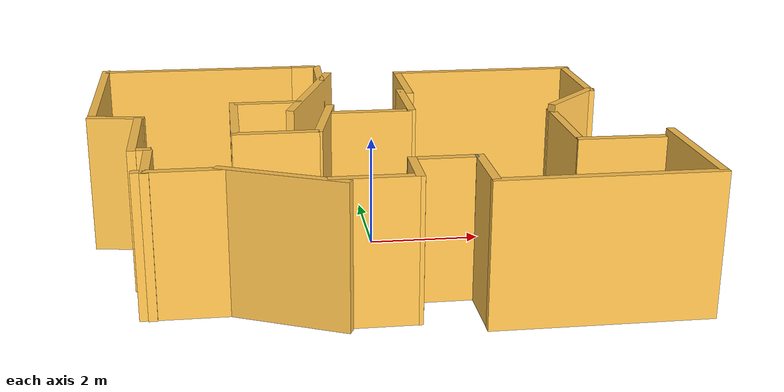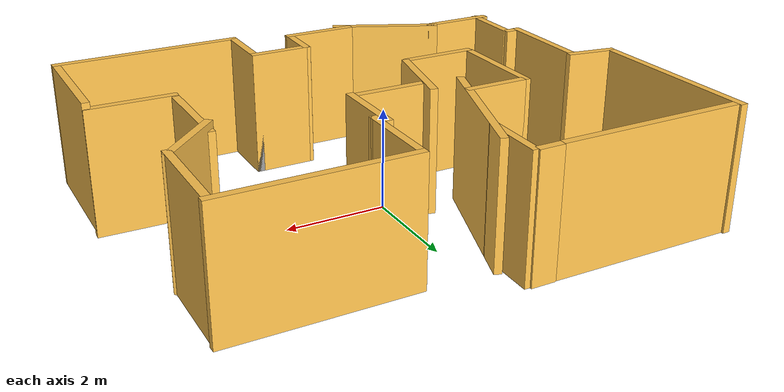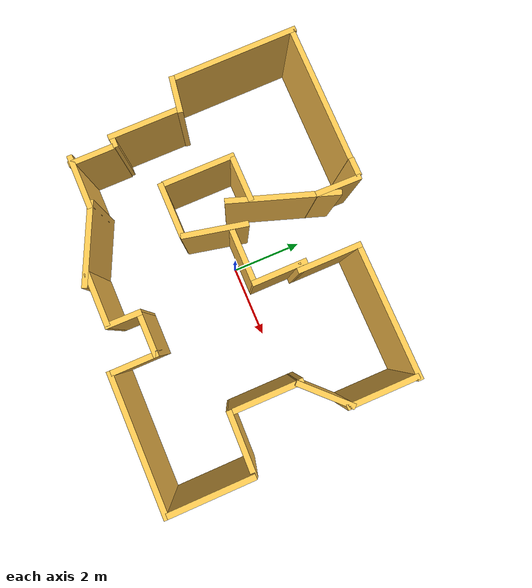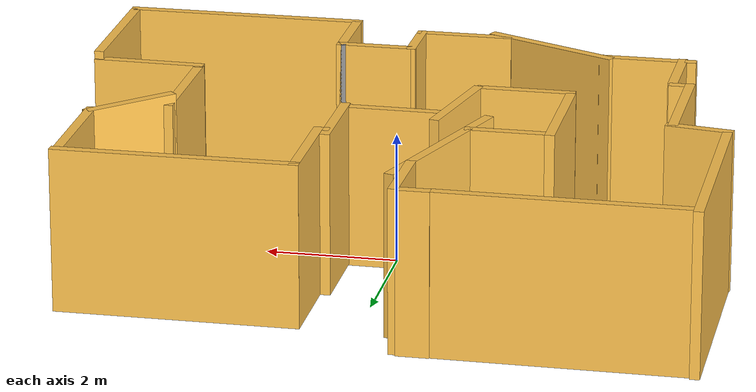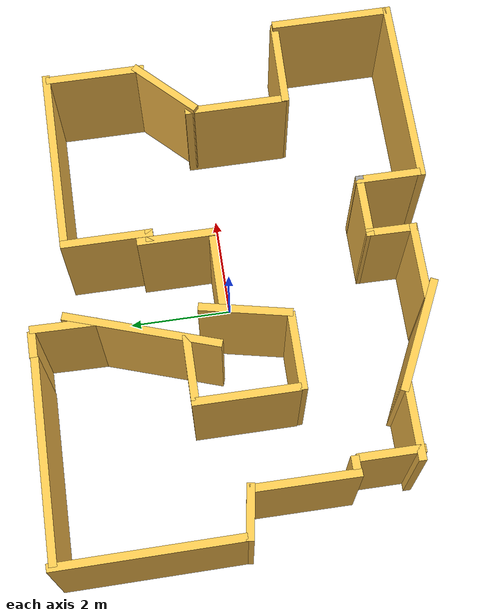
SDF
<?xml version='1.0'?>
<sdf version='1.6'>
  <model name='OrangeWorld'>
    <link name='Wall_0'>
      <pose frame=''>5.01158 -2.74468 0 0 -0 1.57358</pose>
      <self_collide>0</self_collide>
      <kinematic>0</kinematic>
      <visual name='Wall_0_Visual'>
        <pose frame=''>0 0 1.25 0 -0 0</pose>
        <geometry>
          <box>
            <size>2.30301 0.15 2.5</size>
          </box>
        </geometry>
        <material>
          <script>
            <uri>file://media/materials/scripts/gazebo.material</uri>
            <name>Gazebo/Grey</name>
          </script>
          <ambient>1 0.764706 0.305882 1</ambient>
          <shader type='pixel'/>
          <diffuse>0.7 0.7 0.7 1</diffuse>
          <specular>0.01 0.01 0.01 1</specular>
          <emissive>0 0 0 1</emissive>
        </material>
        <meta>
          <layer>0</layer>
        </meta>
        <transparency>0</transparency>
        <cast_shadows>1</cast_shadows>
      </visual>
      <collision name='Wall_0_Collision'>
        <laser_retro>0</laser_retro>
        <max_contacts>10</max_contacts>
        <pose frame=''>0 0 1.25 0 -0 0</pose>
        <geometry>
          <box>
            <size>2.30301 0.15 2.5</size>
          </box>
        </geometry>
        <surface>
          <friction>
            <ode>
              <mu>1</mu>
              <mu2>1</mu2>
              <fdir1>0 0 0</fdir1>
              <slip1>0</slip1>
              <slip2>0</slip2>
            </ode>
            <torsional>
              <coefficient>1</coefficient>
              <patch_radius>0</patch_radius>
              <surface_radius>0</surface_radius>
              <use_patch_radius>1</use_patch_radius>
              <ode>
                <slip>0</slip>
              </ode>
            </torsional>
          </friction>
          <bounce>
            <restitution_coefficient>0</restitution_coefficient>
            <threshold>1e+06</threshold>
          </bounce>
          <contact>
            <collide_without_contact>0</collide_without_contact>
            <collide_without_contact_bitmask>1</collide_without_contact_bitmask>
            <collide_bitmask>1</collide_bitmask>
            <ode>
              <soft_cfm>0</soft_cfm>
              <soft_erp>0.2</soft_erp>
              <kp>1e+13</kp>
              <kd>1</kd>
              <max_vel>0.01</max_vel>
              <min_depth>0</min_depth>
            </ode>
            <bullet>
              <split_impulse>1</split_impulse>
              <split_impulse_penetration_threshold>-0.01</split_impulse_penetration_threshold>
              <soft_cfm>0</soft_cfm>
              <soft_erp>0.2</soft_erp>
              <kp>1e+13</kp>
              <kd>1</kd>
            </bullet>
          </contact>
        </surface>
      </collision>
    </link>
    <link name='Wall_1'>
      <pose frame=''>4.21704 -1.62322 -0.123 0 -0 3.12118</pose>
      <self_collide>0</self_collide>
      <kinematic>0</kinematic>
      <visual name='Wall_1_Visual'>
        <pose frame=''>0 0 1.25 0 -0 0</pose>
        <geometry>
          <box>
            <size>1.72186 0.15 2.5</size>
          </box>
        </geometry>
        <material>
          <script>
            <uri>file://media/materials/scripts/gazebo.material</uri>
            <name>Gazebo/Grey</name>
          </script>
          <ambient>1 0.764706 0.305882 1</ambient>
          <shader type='pixel'/>
          <diffuse>0.7 0.7 0.7 1</diffuse>
          <specular>0.01 0.01 0.01 1</specular>
          <emissive>0 0 0 1</emissive>
        </material>
        <meta>
          <layer>0</layer>
        </meta>
        <transparency>0</transparency>
        <cast_shadows>1</cast_shadows>
      </visual>
      <collision name='Wall_1_Collision'>
        <laser_retro>0</laser_retro>
        <max_contacts>10</max_contacts>
        <pose frame=''>0 0 1.25 0 -0 0</pose>
        <geometry>
          <box>
            <size>1.72186 0.15 2.5</size>
          </box>
        </geometry>
        <surface>
          <friction>
            <ode>
              <mu>1</mu>
              <mu2>1</mu2>
              <fdir1>0 0 0</fdir1>
              <slip1>0</slip1>
              <slip2>0</slip2>
            </ode>
            <torsional>
              <coefficient>1</coefficient>
              <patch_radius>0</patch_radius>
              <surface_radius>0</surface_radius>
              <use_patch_radius>1</use_patch_radius>
              <ode>
                <slip>0</slip>
              </ode>
            </torsional>
          </friction>
          <bounce>
            <restitution_coefficient>0</restitution_coefficient>
            <threshold>1e+06</threshold>
          </bounce>
          <contact>
            <collide_without_contact>0</collide_without_contact>
            <collide_without_contact_bitmask>1</collide_without_contact_bitmask>
            <collide_bitmask>1</collide_bitmask>
            <ode>
              <soft_cfm>0</soft_cfm>
              <soft_erp>0.2</soft_erp>
              <kp>1e+13</kp>
              <kd>1</kd>
              <max_vel>0.01</max_vel>
              <min_depth>0</min_depth>
            </ode>
            <bullet>
              <split_impulse>1</split_impulse>
              <split_impulse_penetration_threshold>-0.01</split_impulse_penetration_threshold>
              <soft_cfm>0</soft_cfm>
              <soft_erp>0.2</soft_erp>
              <kp>1e+13</kp>
              <kd>1</kd>
            </bullet>
          </contact>
        </surface>
      </collision>
    </link>
    <link name='Wall_10'>
      <pose frame=''>-0.865417 -0.189767 0 0 0 -1.7807</pose>
      <self_collide>0</self_collide>
      <kinematic>0</kinematic>
      <visual name='Wall_10_Visual'>
        <pose frame=''>0 0 1.25 0 -0 0</pose>
        <geometry>
          <box>
            <size>1.75 0.15 2.5</size>
          </box>
        </geometry>
        <material>
          <script>
            <uri>file://media/materials/scripts/gazebo.material</uri>
            <name>Gazebo/Grey</name>
          </script>
          <ambient>1 0.764706 0.305882 1</ambient>
          <shader type='pixel'/>
          <diffuse>0.7 0.7 0.7 1</diffuse>
          <specular>0.01 0.01 0.01 1</specular>
          <emissive>0 0 0 1</emissive>
        </material>
        <meta>
          <layer>0</layer>
        </meta>
        <transparency>0</transparency>
        <cast_shadows>1</cast_shadows>
      </visual>
      <collision name='Wall_10_Collision'>
        <laser_retro>0</laser_retro>
        <max_contacts>10</max_contacts>
        <pose frame=''>0 0 1.25 0 -0 0</pose>
        <geometry>
          <box>
            <size>1.75 0.15 2.5</size>
          </box>
        </geometry>
        <surface>
          <friction>
            <ode>
              <mu>1</mu>
              <mu2>1</mu2>
              <fdir1>0 0 0</fdir1>
              <slip1>0</slip1>
              <slip2>0</slip2>
            </ode>
            <torsional>
              <coefficient>1</coefficient>
              <patch_radius>0</patch_radius>
              <surface_radius>0</surface_radius>
              <use_patch_radius>1</use_patch_radius>
              <ode>
                <slip>0</slip>
              </ode>
            </torsional>
          </friction>
          <bounce>
            <restitution_coefficient>0</restitution_coefficient>
            <threshold>1e+06</threshold>
          </bounce>
          <contact>
            <collide_without_contact>0</collide_without_contact>
            <collide_without_contact_bitmask>1</collide_without_contact_bitmask>
            <collide_bitmask>1</collide_bitmask>
            <ode>
              <soft_cfm>0</soft_cfm>
              <soft_erp>0.2</soft_erp>
              <kp>1e+13</kp>
              <kd>1</kd>
              <max_vel>0.01</max_vel>
              <min_depth>0</min_depth>
            </ode>
            <bullet>
              <split_impulse>1</split_impulse>
              <split_impulse_penetration_threshold>-0.01</split_impulse_penetration_threshold>
              <soft_cfm>0</soft_cfm>
              <soft_erp>0.2</soft_erp>
              <kp>1e+13</kp>
              <kd>1</kd>
            </bullet>
          </contact>
        </surface>
      </collision>
    </link>
    <link name='Wall_11'>
      <pose frame=''>-0.697064 3.1454 0 0 -0 1.55471</pose>
      <self_collide>0</self_collide>
      <kinematic>0</kinematic>
      <visual name='Wall_11_Visual'>
        <pose frame=''>0 0 1.25 0 -0 0</pose>
        <geometry>
          <box>
            <size>1.25 0.15 2.5</size>
          </box>
        </geometry>
        <material>
          <script>
            <uri>file://media/materials/scripts/gazebo.material</uri>
            <name>Gazebo/Grey</name>
          </script>
          <ambient>1 0.764706 0.305882 1</ambient>
          <shader type='pixel'/>
          <diffuse>0.7 0.7 0.7 1</diffuse>
          <specular>0.01 0.01 0.01 1</specular>
          <emissive>0 0 0 1</emissive>
        </material>
        <meta>
          <layer>0</layer>
        </meta>
        <transparency>0</transparency>
        <cast_shadows>1</cast_shadows>
      </visual>
      <collision name='Wall_11_Collision'>
        <laser_retro>0</laser_retro>
        <max_contacts>10</max_contacts>
        <pose frame=''>0 0 1.25 0 -0 0</pose>
        <geometry>
          <box>
            <size>1.25 0.15 2.5</size>
          </box>
        </geometry>
        <surface>
          <friction>
            <ode>
              <mu>1</mu>
              <mu2>1</mu2>
              <fdir1>0 0 0</fdir1>
              <slip1>0</slip1>
              <slip2>0</slip2>
            </ode>
            <torsional>
              <coefficient>1</coefficient>
              <patch_radius>0</patch_radius>
              <surface_radius>0</surface_radius>
              <use_patch_radius>1</use_patch_radius>
              <ode>
                <slip>0</slip>
              </ode>
            </torsional>
          </friction>
          <bounce>
            <restitution_coefficient>0</restitution_coefficient>
            <threshold>1e+06</threshold>
          </bounce>
          <contact>
            <collide_without_contact>0</collide_without_contact>
            <collide_without_contact_bitmask>1</collide_without_contact_bitmask>
            <collide_bitmask>1</collide_bitmask>
            <ode>
              <soft_cfm>0</soft_cfm>
              <soft_erp>0.2</soft_erp>
              <kp>1e+13</kp>
              <kd>1</kd>
              <max_vel>0.01</max_vel>
              <min_depth>0</min_depth>
            </ode>
            <bullet>
              <split_impulse>1</split_impulse>
              <split_impulse_penetration_threshold>-0.01</split_impulse_penetration_threshold>
              <soft_cfm>0</soft_cfm>
              <soft_erp>0.2</soft_erp>
              <kp>1e+13</kp>
              <kd>1</kd>
            </bullet>
          </contact>
        </surface>
      </collision>
    </link>
    <link name='Wall_12'>
      <pose frame=''>0.018082 0.204928 -0.021351 0 -0 3.13458</pose>
      <self_collide>0</self_collide>
      <kinematic>0</kinematic>
      <visual name='Wall_12_Visual'>
        <pose frame=''>0 0 1.25 0 -0 0</pose>
        <geometry>
          <box>
            <size>1.5 0.15 2.5</size>
          </box>
        </geometry>
        <material>
          <script>
            <uri>file://media/materials/scripts/gazebo.material</uri>
            <name>Gazebo/Grey</name>
          </script>
          <ambient>1 0.764706 0.305882 1</ambient>
          <shader type='pixel'/>
          <diffuse>0.7 0.7 0.7 1</diffuse>
          <specular>0.01 0.01 0.01 1</specular>
          <emissive>0 0 0 1</emissive>
        </material>
        <meta>
          <layer>0</layer>
        </meta>
        <transparency>0</transparency>
        <cast_shadows>1</cast_shadows>
      </visual>
      <collision name='Wall_12_Collision'>
        <laser_retro>0</laser_retro>
        <max_contacts>10</max_contacts>
        <pose frame=''>0 0 1.25 0 -0 0</pose>
        <geometry>
          <box>
            <size>1.5 0.15 2.5</size>
          </box>
        </geometry>
        <surface>
          <friction>
            <ode>
              <mu>1</mu>
              <mu2>1</mu2>
              <fdir1>0 0 0</fdir1>
              <slip1>0</slip1>
              <slip2>0</slip2>
            </ode>
            <torsional>
              <coefficient>1</coefficient>
              <patch_radius>0</patch_radius>
              <surface_radius>0</surface_radius>
              <use_patch_radius>1</use_patch_radius>
              <ode>
                <slip>0</slip>
              </ode>
            </torsional>
          </friction>
          <bounce>
            <restitution_coefficient>0</restitution_coefficient>
            <threshold>1e+06</threshold>
          </bounce>
          <contact>
            <collide_without_contact>0</collide_without_contact>
            <collide_without_contact_bitmask>1</collide_without_contact_bitmask>
            <collide_bitmask>1</collide_bitmask>
            <ode>
              <soft_cfm>0</soft_cfm>
              <soft_erp>0.2</soft_erp>
              <kp>1e+13</kp>
              <kd>1</kd>
              <max_vel>0.01</max_vel>
              <min_depth>0</min_depth>
            </ode>
            <bullet>
              <split_impulse>1</split_impulse>
              <split_impulse_penetration_threshold>-0.01</split_impulse_penetration_threshold>
              <soft_cfm>0</soft_cfm>
              <soft_erp>0.2</soft_erp>
              <kp>1e+13</kp>
              <kd>1</kd>
            </bullet>
          </contact>
        </surface>
      </collision>
    </link>
    <link name='Wall_13'>
      <pose frame=''>-1.77414 -1.00395 0 0 -0 3.14159</pose>
      <self_collide>0</self_collide>
      <kinematic>0</kinematic>
      <visual name='Wall_13_Visual'>
        <pose frame=''>0 0 1.25 0 -0 0</pose>
        <geometry>
          <box>
            <size>1.5 0.15 2.5</size>
          </box>
        </geometry>
        <material>
          <script>
            <uri>file://media/materials/scripts/gazebo.material</uri>
            <name>Gazebo/Grey</name>
          </script>
          <ambient>1 0.764706 0.305882 1</ambient>
          <shader type='pixel'/>
          <diffuse>0.7 0.7 0.7 1</diffuse>
          <specular>0.01 0.01 0.01 1</specular>
          <emissive>0 0 0 1</emissive>
        </material>
        <meta>
          <layer>0</layer>
        </meta>
        <transparency>0</transparency>
        <cast_shadows>1</cast_shadows>
      </visual>
      <collision name='Wall_13_Collision'>
        <laser_retro>0</laser_retro>
        <max_contacts>10</max_contacts>
        <pose frame=''>0 0 1.25 0 -0 0</pose>
        <geometry>
          <box>
            <size>1.5 0.15 2.5</size>
          </box>
        </geometry>
        <surface>
          <friction>
            <ode>
              <mu>1</mu>
              <mu2>1</mu2>
              <fdir1>0 0 0</fdir1>
              <slip1>0</slip1>
              <slip2>0</slip2>
            </ode>
            <torsional>
              <coefficient>1</coefficient>
              <patch_radius>0</patch_radius>
              <surface_radius>0</surface_radius>
              <use_patch_radius>1</use_patch_radius>
              <ode>
                <slip>0</slip>
              </ode>
            </torsional>
          </friction>
          <bounce>
            <restitution_coefficient>0</restitution_coefficient>
            <threshold>1e+06</threshold>
          </bounce>
          <contact>
            <collide_without_contact>0</collide_without_contact>
            <collide_without_contact_bitmask>1</collide_without_contact_bitmask>
            <collide_bitmask>1</collide_bitmask>
            <ode>
              <soft_cfm>0</soft_cfm>
              <soft_erp>0.2</soft_erp>
              <kp>1e+13</kp>
              <kd>1</kd>
              <max_vel>0.01</max_vel>
              <min_depth>0</min_depth>
            </ode>
            <bullet>
              <split_impulse>1</split_impulse>
              <split_impulse_penetration_threshold>-0.01</split_impulse_penetration_threshold>
              <soft_cfm>0</soft_cfm>
              <soft_erp>0.2</soft_erp>
              <kp>1e+13</kp>
              <kd>1</kd>
            </bullet>
          </contact>
        </surface>
      </collision>
    </link>
    <link name='Wall_14'>
      <pose frame=''>-2.46413 0.02756 0 0 -0 1.5708</pose>
      <self_collide>0</self_collide>
      <kinematic>0</kinematic>
      <visual name='Wall_14_Visual'>
        <pose frame=''>0 0 1.25 0 -0 0</pose>
        <geometry>
          <box>
            <size>2 0.15 2.5</size>
          </box>
        </geometry>
        <material>
          <script>
            <uri>file://media/materials/scripts/gazebo.material</uri>
            <name>Gazebo/Grey</name>
          </script>
          <ambient>1 0.764706 0.305882 1</ambient>
          <shader type='pixel'/>
          <diffuse>0.7 0.7 0.7 1</diffuse>
          <specular>0.01 0.01 0.01 1</specular>
          <emissive>0 0 0 1</emissive>
        </material>
        <meta>
          <layer>0</layer>
        </meta>
        <transparency>0</transparency>
        <cast_shadows>1</cast_shadows>
      </visual>
      <collision name='Wall_14_Collision'>
        <laser_retro>0</laser_retro>
        <max_contacts>10</max_contacts>
        <pose frame=''>0 0 1.25 0 -0 0</pose>
        <geometry>
          <box>
            <size>2 0.15 2.5</size>
          </box>
        </geometry>
        <surface>
          <friction>
            <ode>
              <mu>1</mu>
              <mu2>1</mu2>
              <fdir1>0 0 0</fdir1>
              <slip1>0</slip1>
              <slip2>0</slip2>
            </ode>
            <torsional>
              <coefficient>1</coefficient>
              <patch_radius>0</patch_radius>
              <surface_radius>0</surface_radius>
              <use_patch_radius>1</use_patch_radius>
              <ode>
                <slip>0</slip>
              </ode>
            </torsional>
          </friction>
          <bounce>
            <restitution_coefficient>0</restitution_coefficient>
            <threshold>1e+06</threshold>
          </bounce>
          <contact>
            <collide_without_contact>0</collide_without_contact>
            <collide_without_contact_bitmask>1</collide_without_contact_bitmask>
            <collide_bitmask>1</collide_bitmask>
            <ode>
              <soft_cfm>0</soft_cfm>
              <soft_erp>0.2</soft_erp>
              <kp>1e+13</kp>
              <kd>1</kd>
              <max_vel>0.01</max_vel>
              <min_depth>0</min_depth>
            </ode>
            <bullet>
              <split_impulse>1</split_impulse>
              <split_impulse_penetration_threshold>-0.01</split_impulse_penetration_threshold>
              <soft_cfm>0</soft_cfm>
              <soft_erp>0.2</soft_erp>
              <kp>1e+13</kp>
              <kd>1</kd>
            </bullet>
          </contact>
        </surface>
      </collision>
    </link>
    <link name='Wall_15'>
      <pose frame=''>-1.81761 0.95256 0 0 -0 0</pose>
      <self_collide>0</self_collide>
      <kinematic>0</kinematic>
      <visual name='Wall_15_Visual'>
        <pose frame=''>0 0 1.25 0 -0 0</pose>
        <geometry>
          <box>
            <size>1.25 0.15 2.5</size>
          </box>
        </geometry>
        <material>
          <script>
            <uri>file://media/materials/scripts/gazebo.material</uri>
            <name>Gazebo/Grey</name>
          </script>
          <ambient>1 0.764706 0.305882 1</ambient>
          <shader type='pixel'/>
          <diffuse>0.7 0.7 0.7 1</diffuse>
          <specular>0.01 0.01 0.01 1</specular>
          <emissive>0 0 0 1</emissive>
        </material>
        <meta>
          <layer>0</layer>
        </meta>
        <transparency>0</transparency>
        <cast_shadows>1</cast_shadows>
      </visual>
      <collision name='Wall_15_Collision'>
        <laser_retro>0</laser_retro>
        <max_contacts>10</max_contacts>
        <pose frame=''>0 0 1.25 0 -0 0</pose>
        <geometry>
          <box>
            <size>1.25 0.15 2.5</size>
          </box>
        </geometry>
        <surface>
          <friction>
            <ode>
              <mu>1</mu>
              <mu2>1</mu2>
              <fdir1>0 0 0</fdir1>
              <slip1>0</slip1>
              <slip2>0</slip2>
            </ode>
            <torsional>
              <coefficient>1</coefficient>
              <patch_radius>0</patch_radius>
              <surface_radius>0</surface_radius>
              <use_patch_radius>1</use_patch_radius>
              <ode>
                <slip>0</slip>
              </ode>
            </torsional>
          </friction>
          <bounce>
            <restitution_coefficient>0</restitution_coefficient>
            <threshold>1e+06</threshold>
          </bounce>
          <contact>
            <collide_without_contact>0</collide_without_contact>
            <collide_without_contact_bitmask>1</collide_without_contact_bitmask>
            <collide_bitmask>1</collide_bitmask>
            <ode>
              <soft_cfm>0</soft_cfm>
              <soft_erp>0.2</soft_erp>
              <kp>1e+13</kp>
              <kd>1</kd>
              <max_vel>0.01</max_vel>
              <min_depth>0</min_depth>
            </ode>
            <bullet>
              <split_impulse>1</split_impulse>
              <split_impulse_penetration_threshold>-0.01</split_impulse_penetration_threshold>
              <soft_cfm>0</soft_cfm>
              <soft_erp>0.2</soft_erp>
              <kp>1e+13</kp>
              <kd>1</kd>
            </bullet>
          </contact>
        </surface>
      </collision>
    </link>
    <link name='Wall_16'>
      <pose frame=''>-0.977098 1.73793 0 0 -0 1.24819</pose>
      <self_collide>0</self_collide>
      <kinematic>0</kinematic>
      <visual name='Wall_16_Visual'>
        <pose frame=''>0 0 1.25 0 -0 0</pose>
        <geometry>
          <box>
            <size>2.99113 0.15 2.5</size>
          </box>
        </geometry>
        <material>
          <script>
            <uri>file://media/materials/scripts/gazebo.material</uri>
            <name>Gazebo/Grey</name>
          </script>
          <ambient>1 0.764706 0.305882 1</ambient>
          <shader type='pixel'/>
          <diffuse>0.7 0.7 0.7 1</diffuse>
          <specular>0.01 0.01 0.01 1</specular>
          <emissive>0 0 0 1</emissive>
        </material>
        <meta>
          <layer>0</layer>
        </meta>
        <transparency>0</transparency>
        <cast_shadows>1</cast_shadows>
      </visual>
      <collision name='Wall_16_Collision'>
        <laser_retro>0</laser_retro>
        <max_contacts>10</max_contacts>
        <pose frame=''>0 0 1.25 0 -0 0</pose>
        <geometry>
          <box>
            <size>2.99113 0.15 2.5</size>
          </box>
        </geometry>
        <surface>
          <friction>
            <ode>
              <mu>1</mu>
              <mu2>1</mu2>
              <fdir1>0 0 0</fdir1>
              <slip1>0</slip1>
              <slip2>0</slip2>
            </ode>
            <torsional>
              <coefficient>1</coefficient>
              <patch_radius>0</patch_radius>
              <surface_radius>0</surface_radius>
              <use_patch_radius>1</use_patch_radius>
              <ode>
                <slip>0</slip>
              </ode>
            </torsional>
          </friction>
          <bounce>
            <restitution_coefficient>0</restitution_coefficient>
            <threshold>1e+06</threshold>
          </bounce>
          <contact>
            <collide_without_contact>0</collide_without_contact>
            <collide_without_contact_bitmask>1</collide_without_contact_bitmask>
            <collide_bitmask>1</collide_bitmask>
            <ode>
              <soft_cfm>0</soft_cfm>
              <soft_erp>0.2</soft_erp>
              <kp>1e+13</kp>
              <kd>1</kd>
              <max_vel>0.01</max_vel>
              <min_depth>0</min_depth>
            </ode>
            <bullet>
              <split_impulse>1</split_impulse>
              <split_impulse_penetration_threshold>-0.01</split_impulse_penetration_threshold>
              <soft_cfm>0</soft_cfm>
              <soft_erp>0.2</soft_erp>
              <kp>1e+13</kp>
              <kd>1</kd>
            </bullet>
          </contact>
        </surface>
      </collision>
    </link>
    <link name='Wall_17'>
      <pose frame=''>-3.11348 3.73571 0 0 -0 3.13412</pose>
      <self_collide>0</self_collide>
      <kinematic>0</kinematic>
      <visual name='Wall_17_Visual'>
        <pose frame=''>0 0 1.25 0 -0 0</pose>
        <geometry>
          <box>
            <size>3.80016 0.15 2.5</size>
          </box>
        </geometry>
        <material>
          <script>
            <uri>file://media/materials/scripts/gazebo.material</uri>
            <name>Gazebo/Grey</name>
          </script>
          <ambient>1 0.764706 0.305882 1</ambient>
          <shader type='pixel'/>
          <diffuse>0.7 0.7 0.7 1</diffuse>
          <specular>0.01 0.01 0.01 1</specular>
          <emissive>0 0 0 1</emissive>
        </material>
        <meta>
          <layer>0</layer>
        </meta>
        <transparency>0</transparency>
        <cast_shadows>1</cast_shadows>
      </visual>
      <collision name='Wall_17_Collision'>
        <laser_retro>0</laser_retro>
        <max_contacts>10</max_contacts>
        <pose frame=''>0 0 1.25 0 -0 0</pose>
        <geometry>
          <box>
            <size>3.80016 0.15 2.5</size>
          </box>
        </geometry>
        <surface>
          <friction>
            <ode>
              <mu>1</mu>
              <mu2>1</mu2>
              <fdir1>0 0 0</fdir1>
              <slip1>0</slip1>
              <slip2>0</slip2>
            </ode>
            <torsional>
              <coefficient>1</coefficient>
              <patch_radius>0</patch_radius>
              <surface_radius>0</surface_radius>
              <use_patch_radius>1</use_patch_radius>
              <ode>
                <slip>0</slip>
              </ode>
            </torsional>
          </friction>
          <bounce>
            <restitution_coefficient>0</restitution_coefficient>
            <threshold>1e+06</threshold>
          </bounce>
          <contact>
            <collide_without_contact>0</collide_without_contact>
            <collide_without_contact_bitmask>1</collide_without_contact_bitmask>
            <collide_bitmask>1</collide_bitmask>
            <ode>
              <soft_cfm>0</soft_cfm>
              <soft_erp>0.2</soft_erp>
              <kp>1e+13</kp>
              <kd>1</kd>
              <max_vel>0.01</max_vel>
              <min_depth>0</min_depth>
            </ode>
            <bullet>
              <split_impulse>1</split_impulse>
              <split_impulse_penetration_threshold>-0.01</split_impulse_penetration_threshold>
              <soft_cfm>0</soft_cfm>
              <soft_erp>0.2</soft_erp>
              <kp>1e+13</kp>
              <kd>1</kd>
            </bullet>
          </contact>
        </surface>
      </collision>
    </link>
    <link name='Wall_18'>
      <pose frame=''>-5.00054 2.12306 0 0 0 -1.56263</pose>
      <self_collide>0</self_collide>
      <kinematic>0</kinematic>
      <visual name='Wall_18_Visual'>
        <pose frame=''>0 0 1.25 0 -0 0</pose>
        <geometry>
          <box>
            <size>3.49111 0.15 2.5</size>
          </box>
        </geometry>
        <material>
          <script>
            <uri>file://media/materials/scripts/gazebo.material</uri>
            <name>Gazebo/Grey</name>
          </script>
          <ambient>1 0.764706 0.305882 1</ambient>
          <shader type='pixel'/>
          <diffuse>0.7 0.7 0.7 1</diffuse>
          <specular>0.01 0.01 0.01 1</specular>
          <emissive>0 0 0 1</emissive>
        </material>
        <meta>
          <layer>0</layer>
        </meta>
        <transparency>0</transparency>
        <cast_shadows>1</cast_shadows>
      </visual>
      <collision name='Wall_18_Collision'>
        <laser_retro>0</laser_retro>
        <max_contacts>10</max_contacts>
        <pose frame=''>0 0 1.25 0 -0 0</pose>
        <geometry>
          <box>
            <size>3.49111 0.15 2.5</size>
          </box>
        </geometry>
        <surface>
          <friction>
            <ode>
              <mu>1</mu>
              <mu2>1</mu2>
              <fdir1>0 0 0</fdir1>
              <slip1>0</slip1>
              <slip2>0</slip2>
            </ode>
            <torsional>
              <coefficient>1</coefficient>
              <patch_radius>0</patch_radius>
              <surface_radius>0</surface_radius>
              <use_patch_radius>1</use_patch_radius>
              <ode>
                <slip>0</slip>
              </ode>
            </torsional>
          </friction>
          <bounce>
            <restitution_coefficient>0</restitution_coefficient>
            <threshold>1e+06</threshold>
          </bounce>
          <contact>
            <collide_without_contact>0</collide_without_contact>
            <collide_without_contact_bitmask>1</collide_without_contact_bitmask>
            <collide_bitmask>1</collide_bitmask>
            <ode>
              <soft_cfm>0</soft_cfm>
              <soft_erp>0.2</soft_erp>
              <kp>1e+13</kp>
              <kd>1</kd>
              <max_vel>0.01</max_vel>
              <min_depth>0</min_depth>
            </ode>
            <bullet>
              <split_impulse>1</split_impulse>
              <split_impulse_penetration_threshold>-0.01</split_impulse_penetration_threshold>
              <soft_cfm>0</soft_cfm>
              <soft_erp>0.2</soft_erp>
              <kp>1e+13</kp>
              <kd>1</kd>
            </bullet>
          </contact>
        </surface>
      </collision>
    </link>
    <link name='Wall_19'>
      <pose frame=''>-4.5597 0.267492 0 0 0 -0.15949</pose>
      <self_collide>0</self_collide>
      <kinematic>0</kinematic>
      <visual name='Wall_19_Visual'>
        <pose frame=''>0 0 1.25 0 -0 0</pose>
        <geometry>
          <box>
            <size>1.0232 0.15 2.5</size>
          </box>
        </geometry>
        <material>
          <script>
            <uri>file://media/materials/scripts/gazebo.material</uri>
            <name>Gazebo/Grey</name>
          </script>
          <ambient>1 0.764706 0.305882 1</ambient>
          <shader type='pixel'/>
          <diffuse>0.7 0.7 0.7 1</diffuse>
          <specular>0.01 0.01 0.01 1</specular>
          <emissive>0 0 0 1</emissive>
        </material>
        <meta>
          <layer>0</layer>
        </meta>
        <transparency>0</transparency>
        <cast_shadows>1</cast_shadows>
      </visual>
      <collision name='Wall_19_Collision'>
        <laser_retro>0</laser_retro>
        <max_contacts>10</max_contacts>
        <pose frame=''>0 0 1.25 0 -0 0</pose>
        <geometry>
          <box>
            <size>1.0232 0.15 2.5</size>
          </box>
        </geometry>
        <surface>
          <friction>
            <ode>
              <mu>1</mu>
              <mu2>1</mu2>
              <fdir1>0 0 0</fdir1>
              <slip1>0</slip1>
              <slip2>0</slip2>
            </ode>
            <torsional>
              <coefficient>1</coefficient>
              <patch_radius>0</patch_radius>
              <surface_radius>0</surface_radius>
              <use_patch_radius>1</use_patch_radius>
              <ode>
                <slip>0</slip>
              </ode>
            </torsional>
          </friction>
          <bounce>
            <restitution_coefficient>0</restitution_coefficient>
            <threshold>1e+06</threshold>
          </bounce>
          <contact>
            <collide_without_contact>0</collide_without_contact>
            <collide_without_contact_bitmask>1</collide_without_contact_bitmask>
            <collide_bitmask>1</collide_bitmask>
            <ode>
              <soft_cfm>0</soft_cfm>
              <soft_erp>0.2</soft_erp>
              <kp>1e+13</kp>
              <kd>1</kd>
              <max_vel>0.01</max_vel>
              <min_depth>0</min_depth>
            </ode>
            <bullet>
              <split_impulse>1</split_impulse>
              <split_impulse_penetration_threshold>-0.01</split_impulse_penetration_threshold>
              <soft_cfm>0</soft_cfm>
              <soft_erp>0.2</soft_erp>
              <kp>1e+13</kp>
              <kd>1</kd>
            </bullet>
          </contact>
        </surface>
      </collision>
    </link>
    <link name='Wall_2'>
      <pose frame=''>3.42333 -0.629117 -0.136708 0 -0 1.5708</pose>
      <self_collide>0</self_collide>
      <kinematic>0</kinematic>
      <visual name='Wall_2_Visual'>
        <pose frame=''>0 0 1.25 0 -0 0</pose>
        <geometry>
          <box>
            <size>2 0.15 2.5</size>
          </box>
        </geometry>
        <material>
          <script>
            <uri>file://media/materials/scripts/gazebo.material</uri>
            <name>Gazebo/Grey</name>
          </script>
          <ambient>1 0.764706 0.305882 1</ambient>
          <shader type='pixel'/>
          <diffuse>0.7 0.7 0.7 1</diffuse>
          <specular>0.01 0.01 0.01 1</specular>
          <emissive>0 0 0 1</emissive>
        </material>
        <meta>
          <layer>0</layer>
        </meta>
        <transparency>0</transparency>
        <cast_shadows>1</cast_shadows>
      </visual>
      <collision name='Wall_2_Collision'>
        <laser_retro>0</laser_retro>
        <max_contacts>10</max_contacts>
        <pose frame=''>0 0 1.25 0 -0 0</pose>
        <geometry>
          <box>
            <size>2 0.15 2.5</size>
          </box>
        </geometry>
        <surface>
          <friction>
            <ode>
              <mu>1</mu>
              <mu2>1</mu2>
              <fdir1>0 0 0</fdir1>
              <slip1>0</slip1>
              <slip2>0</slip2>
            </ode>
            <torsional>
              <coefficient>1</coefficient>
              <patch_radius>0</patch_radius>
              <surface_radius>0</surface_radius>
              <use_patch_radius>1</use_patch_radius>
              <ode>
                <slip>0</slip>
              </ode>
            </torsional>
          </friction>
          <bounce>
            <restitution_coefficient>0</restitution_coefficient>
            <threshold>1e+06</threshold>
          </bounce>
          <contact>
            <collide_without_contact>0</collide_without_contact>
            <collide_without_contact_bitmask>1</collide_without_contact_bitmask>
            <collide_bitmask>1</collide_bitmask>
            <ode>
              <soft_cfm>0</soft_cfm>
              <soft_erp>0.2</soft_erp>
              <kp>1e+13</kp>
              <kd>1</kd>
              <max_vel>0.01</max_vel>
              <min_depth>0</min_depth>
            </ode>
            <bullet>
              <split_impulse>1</split_impulse>
              <split_impulse_penetration_threshold>-0.01</split_impulse_penetration_threshold>
              <soft_cfm>0</soft_cfm>
              <soft_erp>0.2</soft_erp>
              <kp>1e+13</kp>
              <kd>1</kd>
            </bullet>
          </contact>
        </surface>
      </collision>
    </link>
    <link name='Wall_20'>
      <pose frame=''>-4.15939 -0.779132 0 0 0 -1.5708</pose>
      <self_collide>0</self_collide>
      <kinematic>0</kinematic>
      <visual name='Wall_20_Visual'>
        <pose frame=''>0 0 1.25 0 -0 0</pose>
        <geometry>
          <box>
            <size>2 0.15 2.5</size>
          </box>
        </geometry>
        <material>
          <script>
            <uri>file://media/materials/scripts/gazebo.material</uri>
            <name>Gazebo/Grey</name>
          </script>
          <ambient>1 0.764706 0.305882 1</ambient>
          <shader type='pixel'/>
          <diffuse>0.7 0.7 0.7 1</diffuse>
          <specular>0.01 0.01 0.01 1</specular>
          <emissive>0 0 0 1</emissive>
        </material>
        <meta>
          <layer>0</layer>
        </meta>
        <transparency>0</transparency>
        <cast_shadows>1</cast_shadows>
      </visual>
      <collision name='Wall_20_Collision'>
        <laser_retro>0</laser_retro>
        <max_contacts>10</max_contacts>
        <pose frame=''>0 0 1.25 0 -0 0</pose>
        <geometry>
          <box>
            <size>2 0.15 2.5</size>
          </box>
        </geometry>
        <surface>
          <friction>
            <ode>
              <mu>1</mu>
              <mu2>1</mu2>
              <fdir1>0 0 0</fdir1>
              <slip1>0</slip1>
              <slip2>0</slip2>
            </ode>
            <torsional>
              <coefficient>1</coefficient>
              <patch_radius>0</patch_radius>
              <surface_radius>0</surface_radius>
              <use_patch_radius>1</use_patch_radius>
              <ode>
                <slip>0</slip>
              </ode>
            </torsional>
          </friction>
          <bounce>
            <restitution_coefficient>0</restitution_coefficient>
            <threshold>1e+06</threshold>
          </bounce>
          <contact>
            <collide_without_contact>0</collide_without_contact>
            <collide_without_contact_bitmask>1</collide_without_contact_bitmask>
            <collide_bitmask>1</collide_bitmask>
            <ode>
              <soft_cfm>0</soft_cfm>
              <soft_erp>0.2</soft_erp>
              <kp>1e+13</kp>
              <kd>1</kd>
              <max_vel>0.01</max_vel>
              <min_depth>0</min_depth>
            </ode>
            <bullet>
              <split_impulse>1</split_impulse>
              <split_impulse_penetration_threshold>-0.01</split_impulse_penetration_threshold>
              <soft_cfm>0</soft_cfm>
              <soft_erp>0.2</soft_erp>
              <kp>1e+13</kp>
              <kd>1</kd>
            </bullet>
          </contact>
        </surface>
      </collision>
    </link>
    <link name='Wall_21'>
      <pose frame=''>-3.96799 -1.69168 0 0 -0 3.14159</pose>
      <self_collide>0</self_collide>
      <kinematic>0</kinematic>
      <visual name='Wall_21_Visual'>
        <pose frame=''>0 0 1.25 0 -0 0</pose>
        <geometry>
          <box>
            <size>0.25 0.15 2.5</size>
          </box>
        </geometry>
        <material>
          <script>
            <uri>file://media/materials/scripts/gazebo.material</uri>
            <name>Gazebo/Grey</name>
          </script>
          <ambient>1 0.764706 0.305882 1</ambient>
          <shader type='pixel'/>
          <diffuse>0.7 0.7 0.7 1</diffuse>
          <specular>0.01 0.01 0.01 1</specular>
          <emissive>0 0 0 1</emissive>
        </material>
        <meta>
          <layer>0</layer>
        </meta>
        <transparency>0</transparency>
        <cast_shadows>1</cast_shadows>
      </visual>
      <collision name='Wall_21_Collision'>
        <laser_retro>0</laser_retro>
        <max_contacts>10</max_contacts>
        <pose frame=''>0 0 1.25 0 -0 0</pose>
        <geometry>
          <box>
            <size>0.25 0.15 2.5</size>
          </box>
        </geometry>
        <surface>
          <friction>
            <ode>
              <mu>1</mu>
              <mu2>1</mu2>
              <fdir1>0 0 0</fdir1>
              <slip1>0</slip1>
              <slip2>0</slip2>
            </ode>
            <torsional>
              <coefficient>1</coefficient>
              <patch_radius>0</patch_radius>
              <surface_radius>0</surface_radius>
              <use_patch_radius>1</use_patch_radius>
              <ode>
                <slip>0</slip>
              </ode>
            </torsional>
          </friction>
          <bounce>
            <restitution_coefficient>0</restitution_coefficient>
            <threshold>1e+06</threshold>
          </bounce>
          <contact>
            <collide_without_contact>0</collide_without_contact>
            <collide_without_contact_bitmask>1</collide_without_contact_bitmask>
            <collide_bitmask>1</collide_bitmask>
            <ode>
              <soft_cfm>0</soft_cfm>
              <soft_erp>0.2</soft_erp>
              <kp>1e+13</kp>
              <kd>1</kd>
              <max_vel>0.01</max_vel>
              <min_depth>0</min_depth>
            </ode>
            <bullet>
              <split_impulse>1</split_impulse>
              <split_impulse_penetration_threshold>-0.01</split_impulse_penetration_threshold>
              <soft_cfm>0</soft_cfm>
              <soft_erp>0.2</soft_erp>
              <kp>1e+13</kp>
              <kd>1</kd>
            </bullet>
          </contact>
        </surface>
      </collision>
    </link>
    <link name='Wall_22'>
      <pose frame=''>-3.89127 -2.34286 0 0 0 -1.5708</pose>
      <self_collide>0</self_collide>
      <kinematic>0</kinematic>
      <visual name='Wall_22_Visual'>
        <pose frame=''>0 0 1.25 0 -0 0</pose>
        <geometry>
          <box>
            <size>1.25 0.15 2.5</size>
          </box>
        </geometry>
        <material>
          <script>
            <uri>file://media/materials/scripts/gazebo.material</uri>
            <name>Gazebo/Grey</name>
          </script>
          <ambient>1 0.764706 0.305882 1</ambient>
          <shader type='pixel'/>
          <diffuse>0.7 0.7 0.7 1</diffuse>
          <specular>0.01 0.01 0.01 1</specular>
          <emissive>0 0 0 1</emissive>
        </material>
        <meta>
          <layer>0</layer>
        </meta>
        <transparency>0</transparency>
        <cast_shadows>1</cast_shadows>
      </visual>
      <collision name='Wall_22_Collision'>
        <laser_retro>0</laser_retro>
        <max_contacts>10</max_contacts>
        <pose frame=''>0 0 1.25 0 -0 0</pose>
        <geometry>
          <box>
            <size>1.25 0.15 2.5</size>
          </box>
        </geometry>
        <surface>
          <friction>
            <ode>
              <mu>1</mu>
              <mu2>1</mu2>
              <fdir1>0 0 0</fdir1>
              <slip1>0</slip1>
              <slip2>0</slip2>
            </ode>
            <torsional>
              <coefficient>1</coefficient>
              <patch_radius>0</patch_radius>
              <surface_radius>0</surface_radius>
              <use_patch_radius>1</use_patch_radius>
              <ode>
                <slip>0</slip>
              </ode>
            </torsional>
          </friction>
          <bounce>
            <restitution_coefficient>0</restitution_coefficient>
            <threshold>1e+06</threshold>
          </bounce>
          <contact>
            <collide_without_contact>0</collide_without_contact>
            <collide_without_contact_bitmask>1</collide_without_contact_bitmask>
            <collide_bitmask>1</collide_bitmask>
            <ode>
              <soft_cfm>0</soft_cfm>
              <soft_erp>0.2</soft_erp>
              <kp>1e+13</kp>
              <kd>1</kd>
              <max_vel>0.01</max_vel>
              <min_depth>0</min_depth>
            </ode>
            <bullet>
              <split_impulse>1</split_impulse>
              <split_impulse_penetration_threshold>-0.01</split_impulse_penetration_threshold>
              <soft_cfm>0</soft_cfm>
              <soft_erp>0.2</soft_erp>
              <kp>1e+13</kp>
              <kd>1</kd>
            </bullet>
          </contact>
        </surface>
      </collision>
    </link>
    <link name='Wall_23'>
      <pose frame=''>-3.35896 -2.86613 0 0 -0 0</pose>
      <self_collide>0</self_collide>
      <kinematic>0</kinematic>
      <visual name='Wall_23_Visual'>
        <pose frame=''>0 0 1.25 0 -0 0</pose>
        <geometry>
          <box>
            <size>1.5 0.15 2.5</size>
          </box>
        </geometry>
        <material>
          <script>
            <uri>file://media/materials/scripts/gazebo.material</uri>
            <name>Gazebo/Grey</name>
          </script>
          <ambient>1 0.764706 0.305882 1</ambient>
          <shader type='pixel'/>
          <diffuse>0.7 0.7 0.7 1</diffuse>
          <specular>0.01 0.01 0.01 1</specular>
          <emissive>0 0 0 1</emissive>
        </material>
        <meta>
          <layer>0</layer>
        </meta>
        <transparency>0</transparency>
        <cast_shadows>1</cast_shadows>
      </visual>
      <collision name='Wall_23_Collision'>
        <laser_retro>0</laser_retro>
        <max_contacts>10</max_contacts>
        <pose frame=''>0 0 1.25 0 -0 0</pose>
        <geometry>
          <box>
            <size>1.5 0.15 2.5</size>
          </box>
        </geometry>
        <surface>
          <friction>
            <ode>
              <mu>1</mu>
              <mu2>1</mu2>
              <fdir1>0 0 0</fdir1>
              <slip1>0</slip1>
              <slip2>0</slip2>
            </ode>
            <torsional>
              <coefficient>1</coefficient>
              <patch_radius>0</patch_radius>
              <surface_radius>0</surface_radius>
              <use_patch_radius>1</use_patch_radius>
              <ode>
                <slip>0</slip>
              </ode>
            </torsional>
          </friction>
          <bounce>
            <restitution_coefficient>0</restitution_coefficient>
            <threshold>1e+06</threshold>
          </bounce>
          <contact>
            <collide_without_contact>0</collide_without_contact>
            <collide_without_contact_bitmask>1</collide_without_contact_bitmask>
            <collide_bitmask>1</collide_bitmask>
            <ode>
              <soft_cfm>0</soft_cfm>
              <soft_erp>0.2</soft_erp>
              <kp>1e+13</kp>
              <kd>1</kd>
              <max_vel>0.01</max_vel>
              <min_depth>0</min_depth>
            </ode>
            <bullet>
              <split_impulse>1</split_impulse>
              <split_impulse_penetration_threshold>-0.01</split_impulse_penetration_threshold>
              <soft_cfm>0</soft_cfm>
              <soft_erp>0.2</soft_erp>
              <kp>1e+13</kp>
              <kd>1</kd>
            </bullet>
          </contact>
        </surface>
      </collision>
    </link>
    <link name='Wall_24'>
      <pose frame=''>-1.79478 -3.25662 0 0 0 -0.438106</pose>
      <self_collide>0</self_collide>
      <kinematic>0</kinematic>
      <visual name='Wall_24_Visual'>
        <pose frame=''>0 0 1.25 0 -0 0</pose>
        <geometry>
          <box>
            <size>2.25 0.15 2.5</size>
          </box>
        </geometry>
        <material>
          <script>
            <uri>file://media/materials/scripts/gazebo.material</uri>
            <name>Gazebo/Grey</name>
          </script>
          <ambient>1 0.764706 0.305882 1</ambient>
          <shader type='pixel'/>
          <diffuse>0.7 0.7 0.7 1</diffuse>
          <specular>0.01 0.01 0.01 1</specular>
          <emissive>0 0 0 1</emissive>
        </material>
        <meta>
          <layer>0</layer>
        </meta>
        <transparency>0</transparency>
        <cast_shadows>1</cast_shadows>
      </visual>
      <collision name='Wall_24_Collision'>
        <laser_retro>0</laser_retro>
        <max_contacts>10</max_contacts>
        <pose frame=''>0 0 1.25 0 -0 0</pose>
        <geometry>
          <box>
            <size>2.25 0.15 2.5</size>
          </box>
        </geometry>
        <surface>
          <friction>
            <ode>
              <mu>1</mu>
              <mu2>1</mu2>
              <fdir1>0 0 0</fdir1>
              <slip1>0</slip1>
              <slip2>0</slip2>
            </ode>
            <torsional>
              <coefficient>1</coefficient>
              <patch_radius>0</patch_radius>
              <surface_radius>0</surface_radius>
              <use_patch_radius>1</use_patch_radius>
              <ode>
                <slip>0</slip>
              </ode>
            </torsional>
          </friction>
          <bounce>
            <restitution_coefficient>0</restitution_coefficient>
            <threshold>1e+06</threshold>
          </bounce>
          <contact>
            <collide_without_contact>0</collide_without_contact>
            <collide_without_contact_bitmask>1</collide_without_contact_bitmask>
            <collide_bitmask>1</collide_bitmask>
            <ode>
              <soft_cfm>0</soft_cfm>
              <soft_erp>0.2</soft_erp>
              <kp>1e+13</kp>
              <kd>1</kd>
              <max_vel>0.01</max_vel>
              <min_depth>0</min_depth>
            </ode>
            <bullet>
              <split_impulse>1</split_impulse>
              <split_impulse_penetration_threshold>-0.01</split_impulse_penetration_threshold>
              <soft_cfm>0</soft_cfm>
              <soft_erp>0.2</soft_erp>
              <kp>1e+13</kp>
              <kd>1</kd>
            </bullet>
          </contact>
        </surface>
      </collision>
    </link>
    <link name='Wall_25'>
      <pose frame=''>-0.370475 -3.54744 0 0 -0 0</pose>
      <self_collide>0</self_collide>
      <kinematic>0</kinematic>
      <visual name='Wall_25_Visual'>
        <pose frame=''>0 0 1.25 0 -0 0</pose>
        <geometry>
          <box>
            <size>1.5 0.15 2.5</size>
          </box>
        </geometry>
        <material>
          <script>
            <uri>file://media/materials/scripts/gazebo.material</uri>
            <name>Gazebo/Grey</name>
          </script>
          <ambient>1 0.764706 0.305882 1</ambient>
          <shader type='pixel'/>
          <diffuse>0.7 0.7 0.7 1</diffuse>
          <specular>0.01 0.01 0.01 1</specular>
          <emissive>0 0 0 1</emissive>
        </material>
        <meta>
          <layer>0</layer>
        </meta>
        <transparency>0</transparency>
        <cast_shadows>1</cast_shadows>
      </visual>
      <collision name='Wall_25_Collision'>
        <laser_retro>0</laser_retro>
        <max_contacts>10</max_contacts>
        <pose frame=''>0 0 1.25 0 -0 0</pose>
        <geometry>
          <box>
            <size>1.5 0.15 2.5</size>
          </box>
        </geometry>
        <surface>
          <friction>
            <ode>
              <mu>1</mu>
              <mu2>1</mu2>
              <fdir1>0 0 0</fdir1>
              <slip1>0</slip1>
              <slip2>0</slip2>
            </ode>
            <torsional>
              <coefficient>1</coefficient>
              <patch_radius>0</patch_radius>
              <surface_radius>0</surface_radius>
              <use_patch_radius>1</use_patch_radius>
              <ode>
                <slip>0</slip>
              </ode>
            </torsional>
          </friction>
          <bounce>
            <restitution_coefficient>0</restitution_coefficient>
            <threshold>1e+06</threshold>
          </bounce>
          <contact>
            <collide_without_contact>0</collide_without_contact>
            <collide_without_contact_bitmask>1</collide_without_contact_bitmask>
            <collide_bitmask>1</collide_bitmask>
            <ode>
              <soft_cfm>0</soft_cfm>
              <soft_erp>0.2</soft_erp>
              <kp>1e+13</kp>
              <kd>1</kd>
              <max_vel>0.01</max_vel>
              <min_depth>0</min_depth>
            </ode>
            <bullet>
              <split_impulse>1</split_impulse>
              <split_impulse_penetration_threshold>-0.01</split_impulse_penetration_threshold>
              <soft_cfm>0</soft_cfm>
              <soft_erp>0.2</soft_erp>
              <kp>1e+13</kp>
              <kd>1</kd>
            </bullet>
          </contact>
        </surface>
      </collision>
    </link>
    <link name='Wall_26'>
      <pose frame=''>0.309439 -3.13427 0 0 -0 1.5589</pose>
      <self_collide>0</self_collide>
      <kinematic>0</kinematic>
      <visual name='Wall_26_Visual'>
        <pose frame=''>0 0 1.25 0 -0 0</pose>
        <geometry>
          <box>
            <size>0.976401 0.15 2.5</size>
          </box>
        </geometry>
        <material>
          <script>
            <uri>file://media/materials/scripts/gazebo.material</uri>
            <name>Gazebo/Grey</name>
          </script>
          <ambient>1 0.764706 0.305882 1</ambient>
          <shader type='pixel'/>
          <diffuse>0.7 0.7 0.7 1</diffuse>
          <specular>0.01 0.01 0.01 1</specular>
          <emissive>0 0 0 1</emissive>
        </material>
        <meta>
          <layer>0</layer>
        </meta>
        <transparency>0</transparency>
        <cast_shadows>1</cast_shadows>
      </visual>
      <collision name='Wall_26_Collision'>
        <laser_retro>0</laser_retro>
        <max_contacts>10</max_contacts>
        <pose frame=''>0 0 1.25 0 -0 0</pose>
        <geometry>
          <box>
            <size>0.976401 0.15 2.5</size>
          </box>
        </geometry>
        <surface>
          <friction>
            <ode>
              <mu>1</mu>
              <mu2>1</mu2>
              <fdir1>0 0 0</fdir1>
              <slip1>0</slip1>
              <slip2>0</slip2>
            </ode>
            <torsional>
              <coefficient>1</coefficient>
              <patch_radius>0</patch_radius>
              <surface_radius>0</surface_radius>
              <use_patch_radius>1</use_patch_radius>
              <ode>
                <slip>0</slip>
              </ode>
            </torsional>
          </friction>
          <bounce>
            <restitution_coefficient>0</restitution_coefficient>
            <threshold>1e+06</threshold>
          </bounce>
          <contact>
            <collide_without_contact>0</collide_without_contact>
            <collide_without_contact_bitmask>1</collide_without_contact_bitmask>
            <collide_bitmask>1</collide_bitmask>
            <ode>
              <soft_cfm>0</soft_cfm>
              <soft_erp>0.2</soft_erp>
              <kp>1e+13</kp>
              <kd>1</kd>
              <max_vel>0.01</max_vel>
              <min_depth>0</min_depth>
            </ode>
            <bullet>
              <split_impulse>1</split_impulse>
              <split_impulse_penetration_threshold>-0.01</split_impulse_penetration_threshold>
              <soft_cfm>0</soft_cfm>
              <soft_erp>0.2</soft_erp>
              <kp>1e+13</kp>
              <kd>1</kd>
            </bullet>
          </contact>
        </surface>
      </collision>
    </link>
    <link name='Wall_27'>
      <pose frame=''>0.864353 -2.7211 0 0 -0 0</pose>
      <self_collide>0</self_collide>
      <kinematic>0</kinematic>
      <visual name='Wall_27_Visual'>
        <pose frame=''>0 0 1.25 0 -0 0</pose>
        <geometry>
          <box>
            <size>1.25 0.15 2.5</size>
          </box>
        </geometry>
        <material>
          <script>
            <uri>file://media/materials/scripts/gazebo.material</uri>
            <name>Gazebo/Grey</name>
          </script>
          <ambient>1 0.764706 0.305882 1</ambient>
          <shader type='pixel'/>
          <diffuse>0.7 0.7 0.7 1</diffuse>
          <specular>0.01 0.01 0.01 1</specular>
          <emissive>0 0 0 1</emissive>
        </material>
        <meta>
          <layer>0</layer>
        </meta>
        <transparency>0</transparency>
        <cast_shadows>1</cast_shadows>
      </visual>
      <collision name='Wall_27_Collision'>
        <laser_retro>0</laser_retro>
        <max_contacts>10</max_contacts>
        <pose frame=''>0 0 1.25 0 -0 0</pose>
        <geometry>
          <box>
            <size>1.25 0.15 2.5</size>
          </box>
        </geometry>
        <surface>
          <friction>
            <ode>
              <mu>1</mu>
              <mu2>1</mu2>
              <fdir1>0 0 0</fdir1>
              <slip1>0</slip1>
              <slip2>0</slip2>
            </ode>
            <torsional>
              <coefficient>1</coefficient>
              <patch_radius>0</patch_radius>
              <surface_radius>0</surface_radius>
              <use_patch_radius>1</use_patch_radius>
              <ode>
                <slip>0</slip>
              </ode>
            </torsional>
          </friction>
          <bounce>
            <restitution_coefficient>0</restitution_coefficient>
            <threshold>1e+06</threshold>
          </bounce>
          <contact>
            <collide_without_contact>0</collide_without_contact>
            <collide_without_contact_bitmask>1</collide_without_contact_bitmask>
            <collide_bitmask>1</collide_bitmask>
            <ode>
              <soft_cfm>0</soft_cfm>
              <soft_erp>0.2</soft_erp>
              <kp>1e+13</kp>
              <kd>1</kd>
              <max_vel>0.01</max_vel>
              <min_depth>0</min_depth>
            </ode>
            <bullet>
              <split_impulse>1</split_impulse>
              <split_impulse_penetration_threshold>-0.01</split_impulse_penetration_threshold>
              <soft_cfm>0</soft_cfm>
              <soft_erp>0.2</soft_erp>
              <kp>1e+13</kp>
              <kd>1</kd>
            </bullet>
          </contact>
        </surface>
      </collision>
    </link>
    <link name='Wall_28'>
      <pose frame=''>1.41435 -2.7211 0 0 -0 0</pose>
      <self_collide>0</self_collide>
      <kinematic>0</kinematic>
      <visual name='Wall_28_Visual'>
        <pose frame=''>0 0 1.25 0 -0 0</pose>
        <geometry>
          <box>
            <size>0.15 0.15 2.5</size>
          </box>
        </geometry>
        <material>
          <script>
            <uri>file://media/materials/scripts/gazebo.material</uri>
            <name>Gazebo/Grey</name>
          </script>
          <ambient>1 1 1 1</ambient>
          <shader type='pixel'/>
          <diffuse>0.7 0.7 0.7 1</diffuse>
          <specular>0.01 0.01 0.01 1</specular>
          <emissive>0 0 0 1</emissive>
        </material>
        <meta>
          <layer>0</layer>
        </meta>
        <transparency>0</transparency>
        <cast_shadows>1</cast_shadows>
      </visual>
      <collision name='Wall_28_Collision'>
        <laser_retro>0</laser_retro>
        <max_contacts>10</max_contacts>
        <pose frame=''>0 0 1.25 0 -0 0</pose>
        <geometry>
          <box>
            <size>0.15 0.15 2.5</size>
          </box>
        </geometry>
        <surface>
          <friction>
            <ode>
              <mu>1</mu>
              <mu2>1</mu2>
              <fdir1>0 0 0</fdir1>
              <slip1>0</slip1>
              <slip2>0</slip2>
            </ode>
            <torsional>
              <coefficient>1</coefficient>
              <patch_radius>0</patch_radius>
              <surface_radius>0</surface_radius>
              <use_patch_radius>1</use_patch_radius>
              <ode>
                <slip>0</slip>
              </ode>
            </torsional>
          </friction>
          <bounce>
            <restitution_coefficient>0</restitution_coefficient>
            <threshold>1e+06</threshold>
          </bounce>
          <contact>
            <collide_without_contact>0</collide_without_contact>
            <collide_without_contact_bitmask>1</collide_without_contact_bitmask>
            <collide_bitmask>1</collide_bitmask>
            <ode>
              <soft_cfm>0</soft_cfm>
              <soft_erp>0.2</soft_erp>
              <kp>1e+13</kp>
              <kd>1</kd>
              <max_vel>0.01</max_vel>
              <min_depth>0</min_depth>
            </ode>
            <bullet>
              <split_impulse>1</split_impulse>
              <split_impulse_penetration_threshold>-0.01</split_impulse_penetration_threshold>
              <soft_cfm>0</soft_cfm>
              <soft_erp>0.2</soft_erp>
              <kp>1e+13</kp>
              <kd>1</kd>
            </bullet>
          </contact>
        </surface>
      </collision>
    </link>
    <link name='Wall_3'>
      <pose frame=''>3.92482 0.704891 0 0 -0 0.788695</pose>
      <self_collide>0</self_collide>
      <kinematic>0</kinematic>
      <visual name='Wall_3_Visual'>
        <pose frame=''>0 0 1.25 0 -0 0</pose>
        <geometry>
          <box>
            <size>1.53419 0.15 2.5</size>
          </box>
        </geometry>
        <material>
          <script>
            <uri>file://media/materials/scripts/gazebo.material</uri>
            <name>Gazebo/Grey</name>
          </script>
          <ambient>1 0.764706 0.305882 1</ambient>
          <shader type='pixel'/>
          <diffuse>0.7 0.7 0.7 1</diffuse>
          <specular>0.01 0.01 0.01 1</specular>
          <emissive>0 0 0 1</emissive>
        </material>
        <meta>
          <layer>0</layer>
        </meta>
        <transparency>0</transparency>
        <cast_shadows>1</cast_shadows>
      </visual>
      <collision name='Wall_3_Collision'>
        <laser_retro>0</laser_retro>
        <max_contacts>10</max_contacts>
        <pose frame=''>0 0 1.25 0 -0 0</pose>
        <geometry>
          <box>
            <size>1.53419 0.15 2.5</size>
          </box>
        </geometry>
        <surface>
          <friction>
            <ode>
              <mu>1</mu>
              <mu2>1</mu2>
              <fdir1>0 0 0</fdir1>
              <slip1>0</slip1>
              <slip2>0</slip2>
            </ode>
            <torsional>
              <coefficient>1</coefficient>
              <patch_radius>0</patch_radius>
              <surface_radius>0</surface_radius>
              <use_patch_radius>1</use_patch_radius>
              <ode>
                <slip>0</slip>
              </ode>
            </torsional>
          </friction>
          <bounce>
            <restitution_coefficient>0</restitution_coefficient>
            <threshold>1e+06</threshold>
          </bounce>
          <contact>
            <collide_without_contact>0</collide_without_contact>
            <collide_without_contact_bitmask>1</collide_without_contact_bitmask>
            <collide_bitmask>1</collide_bitmask>
            <ode>
              <soft_cfm>0</soft_cfm>
              <soft_erp>0.2</soft_erp>
              <kp>1e+13</kp>
              <kd>1</kd>
              <max_vel>0.01</max_vel>
              <min_depth>0</min_depth>
            </ode>
            <bullet>
              <split_impulse>1</split_impulse>
              <split_impulse_penetration_threshold>-0.01</split_impulse_penetration_threshold>
              <soft_cfm>0</soft_cfm>
              <soft_erp>0.2</soft_erp>
              <kp>1e+13</kp>
              <kd>1</kd>
            </bullet>
          </contact>
        </surface>
      </collision>
    </link>
    <link name='Wall_31'>
      <pose frame=''>1.41599 -3.2711 0 0 0 -1.5708</pose>
      <self_collide>0</self_collide>
      <kinematic>0</kinematic>
      <visual name='Wall_31_Visual'>
        <pose frame=''>0 0 1.25 0 -0 0</pose>
        <geometry>
          <box>
            <size>1.25 0.15 2.5</size>
          </box>
        </geometry>
        <material>
          <script>
            <uri>file://media/materials/scripts/gazebo.material</uri>
            <name>Gazebo/Grey</name>
          </script>
          <ambient>1 0.764706 0.305882 1</ambient>
          <shader type='pixel'/>
          <diffuse>0.7 0.7 0.7 1</diffuse>
          <specular>0.01 0.01 0.01 1</specular>
          <emissive>0 0 0 1</emissive>
        </material>
        <meta>
          <layer>0</layer>
        </meta>
        <transparency>0</transparency>
        <cast_shadows>1</cast_shadows>
      </visual>
      <collision name='Wall_31_Collision'>
        <laser_retro>0</laser_retro>
        <max_contacts>10</max_contacts>
        <pose frame=''>0 0 1.25 0 -0 0</pose>
        <geometry>
          <box>
            <size>1.25 0.15 2.5</size>
          </box>
        </geometry>
        <surface>
          <friction>
            <ode>
              <mu>1</mu>
              <mu2>1</mu2>
              <fdir1>0 0 0</fdir1>
              <slip1>0</slip1>
              <slip2>0</slip2>
            </ode>
            <torsional>
              <coefficient>1</coefficient>
              <patch_radius>0</patch_radius>
              <surface_radius>0</surface_radius>
              <use_patch_radius>1</use_patch_radius>
              <ode>
                <slip>0</slip>
              </ode>
            </torsional>
          </friction>
          <bounce>
            <restitution_coefficient>0</restitution_coefficient>
            <threshold>1e+06</threshold>
          </bounce>
          <contact>
            <collide_without_contact>0</collide_without_contact>
            <collide_without_contact_bitmask>1</collide_without_contact_bitmask>
            <collide_bitmask>1</collide_bitmask>
            <ode>
              <soft_cfm>0</soft_cfm>
              <soft_erp>0.2</soft_erp>
              <kp>1e+13</kp>
              <kd>1</kd>
              <max_vel>0.01</max_vel>
              <min_depth>0</min_depth>
            </ode>
            <bullet>
              <split_impulse>1</split_impulse>
              <split_impulse_penetration_threshold>-0.01</split_impulse_penetration_threshold>
              <soft_cfm>0</soft_cfm>
              <soft_erp>0.2</soft_erp>
              <kp>1e+13</kp>
              <kd>1</kd>
            </bullet>
          </contact>
        </surface>
      </collision>
    </link>
    <link name='Wall_32'>
      <pose frame=''>3.21447 -3.91331 0 0 0 -2.4e-05</pose>
      <self_collide>0</self_collide>
      <kinematic>0</kinematic>
      <visual name='Wall_32_Visual'>
        <pose frame=''>0 0 1.25 0 -0 0</pose>
        <geometry>
          <box>
            <size>3.75 0.15 2.5</size>
          </box>
        </geometry>
        <material>
          <script>
            <uri>file://media/materials/scripts/gazebo.material</uri>
            <name>Gazebo/Grey</name>
          </script>
          <ambient>1 0.764706 0.305882 1</ambient>
          <shader type='pixel'/>
          <diffuse>0.7 0.7 0.7 1</diffuse>
          <specular>0.01 0.01 0.01 1</specular>
          <emissive>0 0 0 1</emissive>
        </material>
        <meta>
          <layer>0</layer>
        </meta>
        <transparency>0</transparency>
        <cast_shadows>1</cast_shadows>
      </visual>
      <collision name='Wall_32_Collision'>
        <laser_retro>0</laser_retro>
        <max_contacts>10</max_contacts>
        <pose frame=''>0 0 1.25 0 -0 0</pose>
        <geometry>
          <box>
            <size>3.75 0.15 2.5</size>
          </box>
        </geometry>
        <surface>
          <friction>
            <ode>
              <mu>1</mu>
              <mu2>1</mu2>
              <fdir1>0 0 0</fdir1>
              <slip1>0</slip1>
              <slip2>0</slip2>
            </ode>
            <torsional>
              <coefficient>1</coefficient>
              <patch_radius>0</patch_radius>
              <surface_radius>0</surface_radius>
              <use_patch_radius>1</use_patch_radius>
              <ode>
                <slip>0</slip>
              </ode>
            </torsional>
          </friction>
          <bounce>
            <restitution_coefficient>0</restitution_coefficient>
            <threshold>1e+06</threshold>
          </bounce>
          <contact>
            <collide_without_contact>0</collide_without_contact>
            <collide_without_contact_bitmask>1</collide_without_contact_bitmask>
            <collide_bitmask>1</collide_bitmask>
            <ode>
              <soft_cfm>0</soft_cfm>
              <soft_erp>0.2</soft_erp>
              <kp>1e+13</kp>
              <kd>1</kd>
              <max_vel>0.01</max_vel>
              <min_depth>0</min_depth>
            </ode>
            <bullet>
              <split_impulse>1</split_impulse>
              <split_impulse_penetration_threshold>-0.01</split_impulse_penetration_threshold>
              <soft_cfm>0</soft_cfm>
              <soft_erp>0.2</soft_erp>
              <kp>1e+13</kp>
              <kd>1</kd>
            </bullet>
          </contact>
        </surface>
      </collision>
    </link>
    <link name='Wall_4'>
      <pose frame=''>4.40597 2.01968 0 0 -0 1.57095</pose>
      <self_collide>0</self_collide>
      <kinematic>0</kinematic>
      <visual name='Wall_4_Visual'>
        <pose frame=''>0 0 1.25 0 -0 0</pose>
        <geometry>
          <box>
            <size>1.93193 0.15 2.5</size>
          </box>
        </geometry>
        <material>
          <script>
            <uri>file://media/materials/scripts/gazebo.material</uri>
            <name>Gazebo/Grey</name>
          </script>
          <ambient>1 0.764706 0.305882 1</ambient>
          <shader type='pixel'/>
          <diffuse>0.7 0.7 0.7 1</diffuse>
          <specular>0.01 0.01 0.01 1</specular>
          <emissive>0 0 0 1</emissive>
        </material>
        <meta>
          <layer>0</layer>
        </meta>
        <transparency>0</transparency>
        <cast_shadows>1</cast_shadows>
      </visual>
      <collision name='Wall_4_Collision'>
        <laser_retro>0</laser_retro>
        <max_contacts>10</max_contacts>
        <pose frame=''>0 0 1.25 0 -0 0</pose>
        <geometry>
          <box>
            <size>1.93193 0.15 2.5</size>
          </box>
        </geometry>
        <surface>
          <friction>
            <ode>
              <mu>1</mu>
              <mu2>1</mu2>
              <fdir1>0 0 0</fdir1>
              <slip1>0</slip1>
              <slip2>0</slip2>
            </ode>
            <torsional>
              <coefficient>1</coefficient>
              <patch_radius>0</patch_radius>
              <surface_radius>0</surface_radius>
              <use_patch_radius>1</use_patch_radius>
              <ode>
                <slip>0</slip>
              </ode>
            </torsional>
          </friction>
          <bounce>
            <restitution_coefficient>0</restitution_coefficient>
            <threshold>1e+06</threshold>
          </bounce>
          <contact>
            <collide_without_contact>0</collide_without_contact>
            <collide_without_contact_bitmask>1</collide_without_contact_bitmask>
            <collide_bitmask>1</collide_bitmask>
            <ode>
              <soft_cfm>0</soft_cfm>
              <soft_erp>0.2</soft_erp>
              <kp>1e+13</kp>
              <kd>1</kd>
              <max_vel>0.01</max_vel>
              <min_depth>0</min_depth>
            </ode>
            <bullet>
              <split_impulse>1</split_impulse>
              <split_impulse_penetration_threshold>-0.01</split_impulse_penetration_threshold>
              <soft_cfm>0</soft_cfm>
              <soft_erp>0.2</soft_erp>
              <kp>1e+13</kp>
              <kd>1</kd>
            </bullet>
          </contact>
        </surface>
      </collision>
    </link>
    <link name='Wall_5'>
      <pose frame=''>2.67208 2.97782 0 0 -0 3.14159</pose>
      <self_collide>0</self_collide>
      <kinematic>0</kinematic>
      <visual name='Wall_5_Visual'>
        <pose frame=''>0 0 1.25 0 -0 0</pose>
        <geometry>
          <box>
            <size>3.68458 0.15 2.5</size>
          </box>
        </geometry>
        <material>
          <script>
            <uri>file://media/materials/scripts/gazebo.material</uri>
            <name>Gazebo/Grey</name>
          </script>
          <ambient>1 0.764706 0.305882 1</ambient>
          <shader type='pixel'/>
          <diffuse>0.7 0.7 0.7 1</diffuse>
          <specular>0.01 0.01 0.01 1</specular>
          <emissive>0 0 0 1</emissive>
        </material>
        <meta>
          <layer>0</layer>
        </meta>
        <transparency>0</transparency>
        <cast_shadows>1</cast_shadows>
      </visual>
      <collision name='Wall_5_Collision'>
        <laser_retro>0</laser_retro>
        <max_contacts>10</max_contacts>
        <pose frame=''>0 0 1.25 0 -0 0</pose>
        <geometry>
          <box>
            <size>3.68458 0.15 2.5</size>
          </box>
        </geometry>
        <surface>
          <friction>
            <ode>
              <mu>1</mu>
              <mu2>1</mu2>
              <fdir1>0 0 0</fdir1>
              <slip1>0</slip1>
              <slip2>0</slip2>
            </ode>
            <torsional>
              <coefficient>1</coefficient>
              <patch_radius>0</patch_radius>
              <surface_radius>0</surface_radius>
              <use_patch_radius>1</use_patch_radius>
              <ode>
                <slip>0</slip>
              </ode>
            </torsional>
          </friction>
          <bounce>
            <restitution_coefficient>0</restitution_coefficient>
            <threshold>1e+06</threshold>
          </bounce>
          <contact>
            <collide_without_contact>0</collide_without_contact>
            <collide_without_contact_bitmask>1</collide_without_contact_bitmask>
            <collide_bitmask>1</collide_bitmask>
            <ode>
              <soft_cfm>0</soft_cfm>
              <soft_erp>0.2</soft_erp>
              <kp>1e+13</kp>
              <kd>1</kd>
              <max_vel>0.01</max_vel>
              <min_depth>0</min_depth>
            </ode>
            <bullet>
              <split_impulse>1</split_impulse>
              <split_impulse_penetration_threshold>-0.01</split_impulse_penetration_threshold>
              <soft_cfm>0</soft_cfm>
              <soft_erp>0.2</soft_erp>
              <kp>1e+13</kp>
              <kd>1</kd>
            </bullet>
          </contact>
        </surface>
      </collision>
    </link>
    <link name='Wall_6'>
      <pose frame=''>0.904794 2.17769 0 0 0 -1.57053</pose>
      <self_collide>0</self_collide>
      <kinematic>0</kinematic>
      <visual name='Wall_6_Visual'>
        <pose frame=''>0 0 1.25 0 -0 0</pose>
        <geometry>
          <box>
            <size>1.75 0.15 2.5</size>
          </box>
        </geometry>
        <material>
          <script>
            <uri>file://media/materials/scripts/gazebo.material</uri>
            <name>Gazebo/Grey</name>
          </script>
          <ambient>1 0.764706 0.305882 1</ambient>
          <shader type='pixel'/>
          <diffuse>0.7 0.7 0.7 1</diffuse>
          <specular>0.01 0.01 0.01 1</specular>
          <emissive>0 0 0 1</emissive>
        </material>
        <meta>
          <layer>0</layer>
        </meta>
        <transparency>0</transparency>
        <cast_shadows>1</cast_shadows>
      </visual>
      <collision name='Wall_6_Collision'>
        <laser_retro>0</laser_retro>
        <max_contacts>10</max_contacts>
        <pose frame=''>0 0 1.25 0 -0 0</pose>
        <geometry>
          <box>
            <size>1.75 0.15 2.5</size>
          </box>
        </geometry>
        <surface>
          <friction>
            <ode>
              <mu>1</mu>
              <mu2>1</mu2>
              <fdir1>0 0 0</fdir1>
              <slip1>0</slip1>
              <slip2>0</slip2>
            </ode>
            <torsional>
              <coefficient>1</coefficient>
              <patch_radius>0</patch_radius>
              <surface_radius>0</surface_radius>
              <use_patch_radius>1</use_patch_radius>
              <ode>
                <slip>0</slip>
              </ode>
            </torsional>
          </friction>
          <bounce>
            <restitution_coefficient>0</restitution_coefficient>
            <threshold>1e+06</threshold>
          </bounce>
          <contact>
            <collide_without_contact>0</collide_without_contact>
            <collide_without_contact_bitmask>1</collide_without_contact_bitmask>
            <collide_bitmask>1</collide_bitmask>
            <ode>
              <soft_cfm>0</soft_cfm>
              <soft_erp>0.2</soft_erp>
              <kp>1e+13</kp>
              <kd>1</kd>
              <max_vel>0.01</max_vel>
              <min_depth>0</min_depth>
            </ode>
            <bullet>
              <split_impulse>1</split_impulse>
              <split_impulse_penetration_threshold>-0.01</split_impulse_penetration_threshold>
              <soft_cfm>0</soft_cfm>
              <soft_erp>0.2</soft_erp>
              <kp>1e+13</kp>
              <kd>1</kd>
            </bullet>
          </contact>
        </surface>
      </collision>
    </link>
    <link name='Wall_7'>
      <pose frame=''>0.855006 1.37756 0 0 -0 3.14159</pose>
      <self_collide>0</self_collide>
      <kinematic>0</kinematic>
      <visual name='Wall_7_Visual'>
        <pose frame=''>0 0 1.25 0 -0 0</pose>
        <geometry>
          <box>
            <size>0.25 0.15 2.5</size>
          </box>
        </geometry>
        <material>
          <script>
            <uri>file://media/materials/scripts/gazebo.material</uri>
            <name>Gazebo/Grey</name>
          </script>
          <ambient>1 0.764706 0.305882 1</ambient>
          <shader type='pixel'/>
          <diffuse>0.7 0.7 0.7 1</diffuse>
          <specular>0.01 0.01 0.01 1</specular>
          <emissive>0 0 0 1</emissive>
        </material>
        <meta>
          <layer>0</layer>
        </meta>
        <transparency>0</transparency>
        <cast_shadows>1</cast_shadows>
      </visual>
      <collision name='Wall_7_Collision'>
        <laser_retro>0</laser_retro>
        <max_contacts>10</max_contacts>
        <pose frame=''>0 0 1.25 0 -0 0</pose>
        <geometry>
          <box>
            <size>0.25 0.15 2.5</size>
          </box>
        </geometry>
        <surface>
          <friction>
            <ode>
              <mu>1</mu>
              <mu2>1</mu2>
              <fdir1>0 0 0</fdir1>
              <slip1>0</slip1>
              <slip2>0</slip2>
            </ode>
            <torsional>
              <coefficient>1</coefficient>
              <patch_radius>0</patch_radius>
              <surface_radius>0</surface_radius>
              <use_patch_radius>1</use_patch_radius>
              <ode>
                <slip>0</slip>
              </ode>
            </torsional>
          </friction>
          <bounce>
            <restitution_coefficient>0</restitution_coefficient>
            <threshold>1e+06</threshold>
          </bounce>
          <contact>
            <collide_without_contact>0</collide_without_contact>
            <collide_without_contact_bitmask>1</collide_without_contact_bitmask>
            <collide_bitmask>1</collide_bitmask>
            <ode>
              <soft_cfm>0</soft_cfm>
              <soft_erp>0.2</soft_erp>
              <kp>1e+13</kp>
              <kd>1</kd>
              <max_vel>0.01</max_vel>
              <min_depth>0</min_depth>
            </ode>
            <bullet>
              <split_impulse>1</split_impulse>
              <split_impulse_penetration_threshold>-0.01</split_impulse_penetration_threshold>
              <soft_cfm>0</soft_cfm>
              <soft_erp>0.2</soft_erp>
              <kp>1e+13</kp>
              <kd>1</kd>
            </bullet>
          </contact>
        </surface>
      </collision>
    </link>
    <link name='Wall_8'>
      <pose frame=''>0.753752 0.877776 0 0 0 -1.5708</pose>
      <self_collide>0</self_collide>
      <kinematic>0</kinematic>
      <visual name='Wall_8_Visual'>
        <pose frame=''>0 0 1.25 0 -0 0</pose>
        <geometry>
          <box>
            <size>1.5 0.15 2.5</size>
          </box>
        </geometry>
        <material>
          <script>
            <uri>file://media/materials/scripts/gazebo.material</uri>
            <name>Gazebo/Grey</name>
          </script>
          <ambient>1 0.764706 0.305882 1</ambient>
          <shader type='pixel'/>
          <diffuse>0.7 0.7 0.7 1</diffuse>
          <specular>0.01 0.01 0.01 1</specular>
          <emissive>0 0 0 1</emissive>
        </material>
        <meta>
          <layer>0</layer>
        </meta>
        <transparency>0</transparency>
        <cast_shadows>1</cast_shadows>
      </visual>
      <collision name='Wall_8_Collision'>
        <laser_retro>0</laser_retro>
        <max_contacts>10</max_contacts>
        <pose frame=''>0 0 1.25 0 -0 0</pose>
        <geometry>
          <box>
            <size>1.5 0.15 2.5</size>
          </box>
        </geometry>
        <surface>
          <friction>
            <ode>
              <mu>1</mu>
              <mu2>1</mu2>
              <fdir1>0 0 0</fdir1>
              <slip1>0</slip1>
              <slip2>0</slip2>
            </ode>
            <torsional>
              <coefficient>1</coefficient>
              <patch_radius>0</patch_radius>
              <surface_radius>0</surface_radius>
              <use_patch_radius>1</use_patch_radius>
              <ode>
                <slip>0</slip>
              </ode>
            </torsional>
          </friction>
          <bounce>
            <restitution_coefficient>0</restitution_coefficient>
            <threshold>1e+06</threshold>
          </bounce>
          <contact>
            <collide_without_contact>0</collide_without_contact>
            <collide_without_contact_bitmask>1</collide_without_contact_bitmask>
            <collide_bitmask>1</collide_bitmask>
            <ode>
              <soft_cfm>0</soft_cfm>
              <soft_erp>0.2</soft_erp>
              <kp>1e+13</kp>
              <kd>1</kd>
              <max_vel>0.01</max_vel>
              <min_depth>0</min_depth>
            </ode>
            <bullet>
              <split_impulse>1</split_impulse>
              <split_impulse_penetration_threshold>-0.01</split_impulse_penetration_threshold>
              <soft_cfm>0</soft_cfm>
              <soft_erp>0.2</soft_erp>
              <kp>1e+13</kp>
              <kd>1</kd>
            </bullet>
          </contact>
        </surface>
      </collision>
    </link>
    <link name='Wall_9'>
      <pose frame=''>-0.971434 3.73552 0 0 -0 -3.13964</pose>
      <self_collide>0</self_collide>
      <kinematic>0</kinematic>
      <visual name='Wall_9_Visual'>
        <pose frame=''>0 0 1.25 0 -0 0</pose>
        <geometry>
          <box>
            <size>0.5 0.15 2.5</size>
          </box>
        </geometry>
        <material>
          <script>
            <uri>file://media/materials/scripts/gazebo.material</uri>
            <name>Gazebo/Grey</name>
          </script>
          <ambient>1 0.764706 0.305882 1</ambient>
          <shader type='pixel'/>
          <diffuse>0.7 0.7 0.7 1</diffuse>
          <specular>0.01 0.01 0.01 1</specular>
          <emissive>0 0 0 1</emissive>
        </material>
        <meta>
          <layer>0</layer>
        </meta>
        <transparency>0</transparency>
        <cast_shadows>1</cast_shadows>
      </visual>
      <collision name='Wall_9_Collision'>
        <laser_retro>0</laser_retro>
        <max_contacts>10</max_contacts>
        <pose frame=''>0 0 1.25 0 -0 0</pose>
        <geometry>
          <box>
            <size>0.5 0.15 2.5</size>
          </box>
        </geometry>
        <surface>
          <friction>
            <ode>
              <mu>1</mu>
              <mu2>1</mu2>
              <fdir1>0 0 0</fdir1>
              <slip1>0</slip1>
              <slip2>0</slip2>
            </ode>
            <torsional>
              <coefficient>1</coefficient>
              <patch_radius>0</patch_radius>
              <surface_radius>0</surface_radius>
              <use_patch_radius>1</use_patch_radius>
              <ode>
                <slip>0</slip>
              </ode>
            </torsional>
          </friction>
          <bounce>
            <restitution_coefficient>0</restitution_coefficient>
            <threshold>1e+06</threshold>
          </bounce>
          <contact>
            <collide_without_contact>0</collide_without_contact>
            <collide_without_contact_bitmask>1</collide_without_contact_bitmask>
            <collide_bitmask>1</collide_bitmask>
            <ode>
              <soft_cfm>0</soft_cfm>
              <soft_erp>0.2</soft_erp>
              <kp>1e+13</kp>
              <kd>1</kd>
              <max_vel>0.01</max_vel>
              <min_depth>0</min_depth>
            </ode>
            <bullet>
              <split_impulse>1</split_impulse>
              <split_impulse_penetration_threshold>-0.01</split_impulse_penetration_threshold>
              <soft_cfm>0</soft_cfm>
              <soft_erp>0.2</soft_erp>
              <kp>1e+13</kp>
              <kd>1</kd>
            </bullet>
          </contact>
        </surface>
      </collision>
    </link>
    <static>1</static>
    <allow_auto_disable>1</allow_auto_disable>
  </model>
</sdf>
